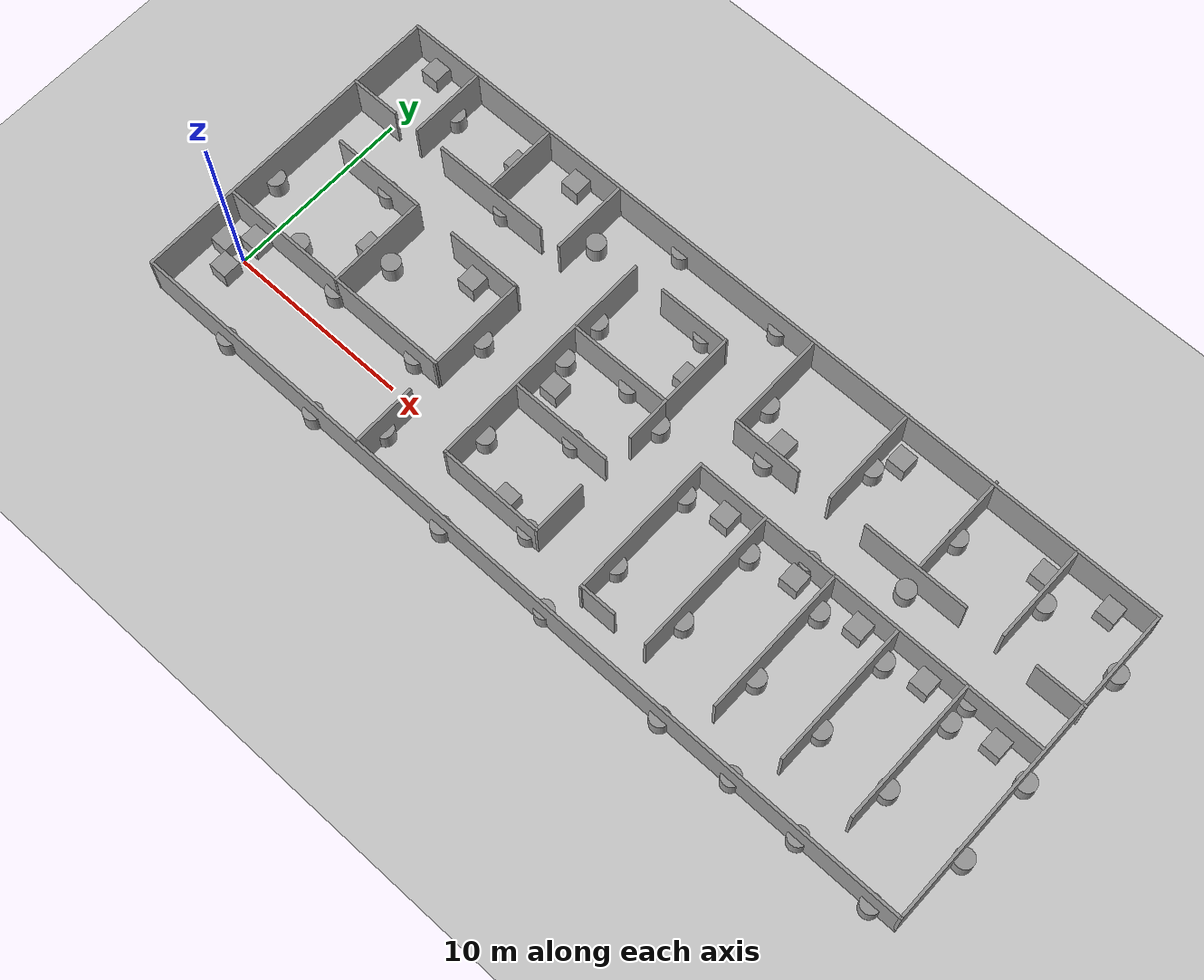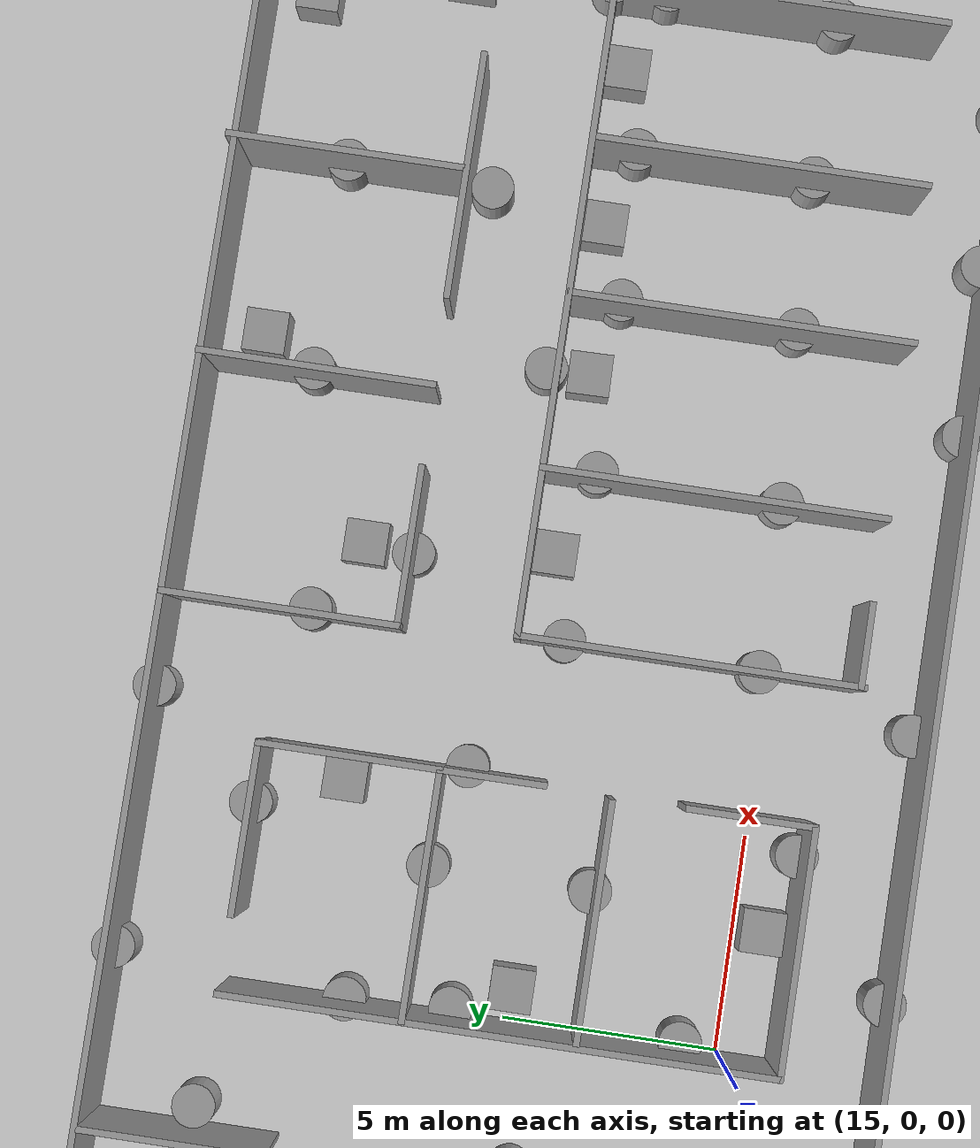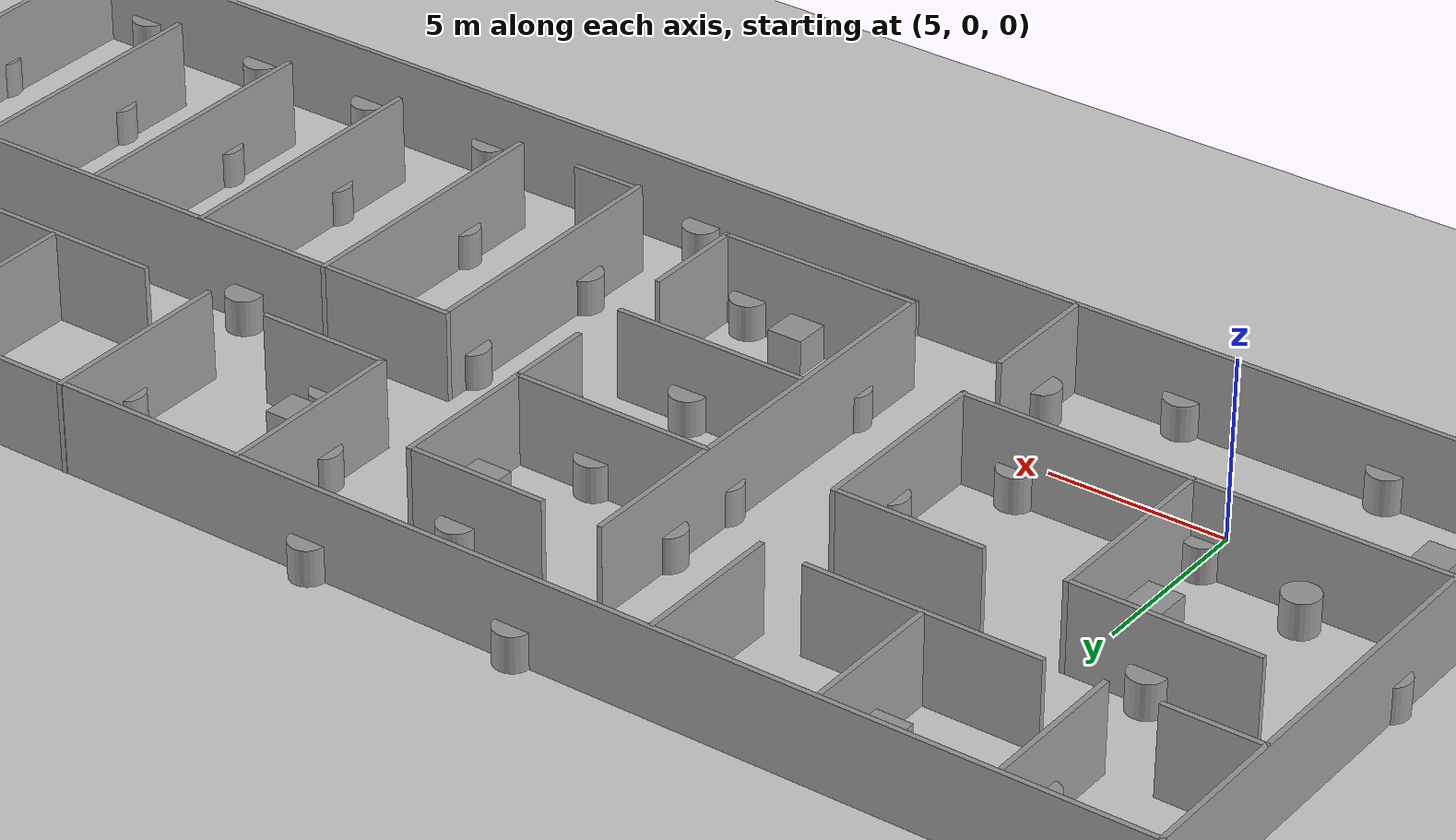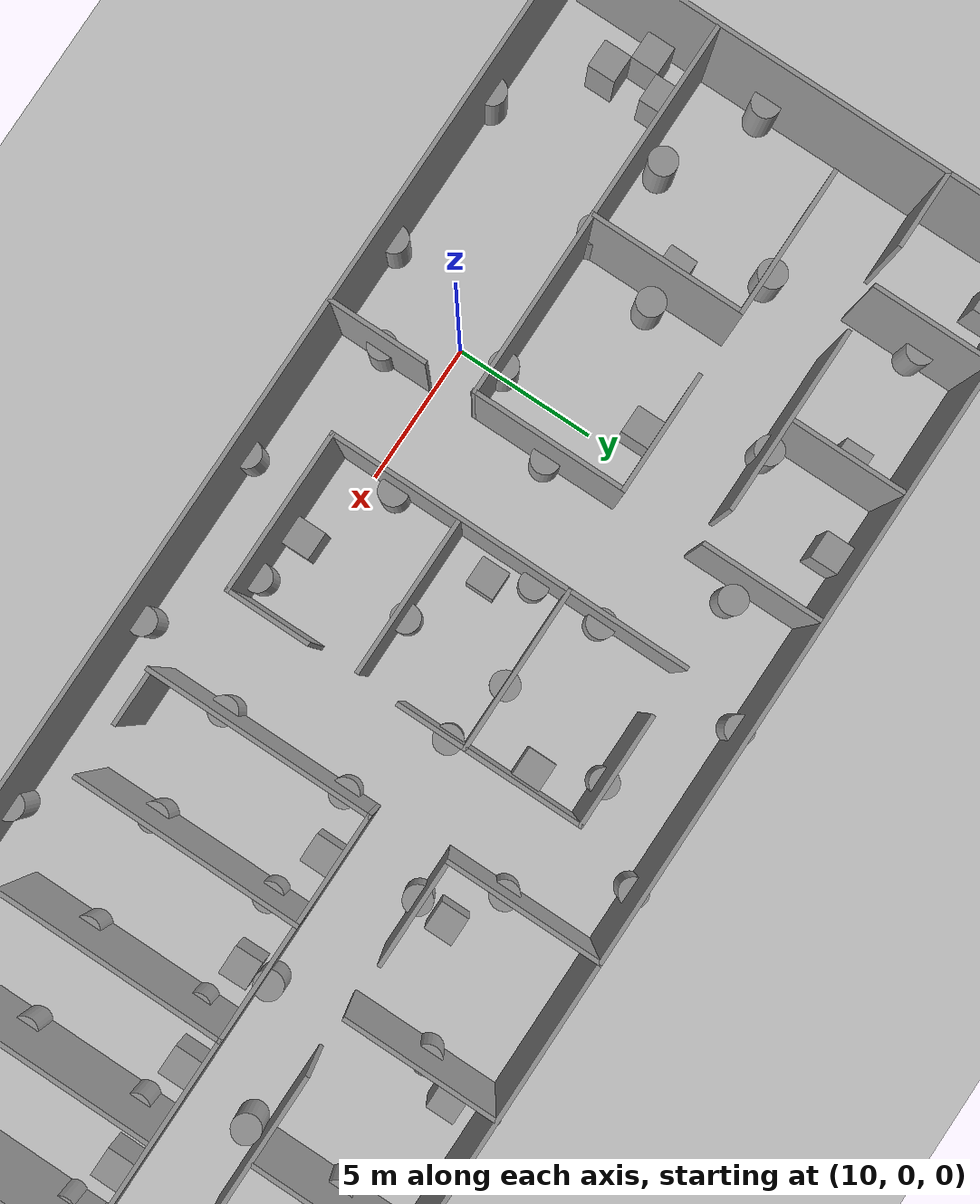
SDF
<sdf version="1.7">
 <world name="default">
  <light name="sun" type="directional">
   <pose>0 0 10 0 -0 0</pose>
   <diffuse>0.8 0.8 0.8 1</diffuse>
   <specular>0.2 0.2 0.2 1</specular>
   <attenuation>
    <range>1000</range>
    <constant>0.9</constant>
    <linear>0.01</linear>
    <quadratic>0.001</quadratic>
   </attenuation>
   <direction>-0.5 0.1 -0.9</direction>
   <spot><inner_angle>0</inner_angle><outer_angle>0</outer_angle><falloff>0</falloff></spot>
  </light>
  <model name="ground_plane">
   <static>1</static>
   <link name="link">
    <collision name="collision">
     <geometry><plane><normal>0 0 1</normal><size>100 100</size></plane></geometry>
     <surface>
      <contact><collide_bitmask>65535</collide_bitmask></contact>
      <friction><ode><mu>100</mu><mu2>50</mu2></ode></friction>
     </surface>
    </collision>
    <visual name="visual">
     <cast_shadows>0</cast_shadows>
     <geometry><plane><normal>0 0 1</normal><size>100 100</size></plane></geometry>
     <material>
      <script><uri>file://media/materials/scripts/gazebo.material</uri><name>Gazebo/Grey</name></script>
     </material>
    </visual>
   </link>
  </model>
  <gravity>0 0 -9.8</gravity>
  <magnetic_field>6e-06 2.3e-05 -4.2e-05</magnetic_field>
  <atmosphere type="adiabatic"/>
  <physics type="ode">
   <max_step_size>0.001</max_step_size>
   <real_time_factor>1</real_time_factor>
   <real_time_update_rate>1000</real_time_update_rate>
  </physics>
  <scene><ambient>0.4 0.4 0.4 1</ambient><background>0.7 0.7 0.7 1</background><shadows>1</shadows></scene>
  <spherical_coordinates>
   <surface_model>EARTH_WGS84</surface_model>
   <latitude_deg>0</latitude_deg>
   <longitude_deg>0</longitude_deg>
   <elevation>0</elevation>
   <heading_deg>0</heading_deg>
  </spherical_coordinates>
  <model name="Lab1">
   <pose>20.7319 5.29666 0 0 -0 0</pose>
   <link name="Wall_1">
    <collision name="Wall_1_Collision">
     <geometry><box><size>45.25 0.15 2.5</size></box></geometry>
     <pose>0 0 1.25 0 -0 0</pose>
    </collision>
    <visual name="Wall_1_Visual">
     <pose>0 0 1.25 0 -0 0</pose>
     <geometry><box><size>45.25 0.15 2.5</size></box></geometry>
     <material>
      <script><uri>file://media/materials/scripts/gazebo.material</uri><name>Gazebo/Grey</name></script>
      <ambient>1 1 1 1</ambient>
     </material>
     <meta><layer>0</layer></meta>
    </visual>
    <pose>-0.042167 -8.8672 0 0 -0 0</pose>
   </link>
   <link name="Wall_10">
    <collision name="Wall_10_Collision">
     <geometry><box><size>6.5 0.15 2.5</size></box></geometry>
     <pose>0 0 1.25 0 -0 0</pose>
    </collision>
    <visual name="Wall_10_Visual">
     <pose>0 0 1.25 0 -0 0</pose>
     <geometry><box><size>6.5 0.15 2.5</size></box></geometry>
     <material>
      <script><uri>file://media/materials/scripts/gazebo.material</uri><name>Gazebo/Grey</name></script>
      <ambient>1 1 1 1</ambient>
     </material>
     <meta><layer>0</layer></meta>
    </visual>
    <pose>-13.6987 4.60775 0 0 -0 0</pose>
   </link>
   <link name="Wall_12">
    <collision name="Wall_12_Collision">
     <geometry><box><size>4 0.15 2.5</size></box></geometry>
     <pose>0 0 1.25 0 -0 0</pose>
    </collision>
    <visual name="Wall_12_Visual">
     <pose>0 0 1.25 0 -0 0</pose>
     <geometry><box><size>4 0.15 2.5</size></box></geometry>
     <material>
      <script><uri>file://media/materials/scripts/gazebo.material</uri><name>Gazebo/Grey</name></script>
      <ambient>1 1 1 1</ambient>
     </material>
     <meta><layer>0</layer></meta>
    </visual>
    <pose>-13.7407 6.65442 0 0 -0 1.5708</pose>
   </link>
   <link name="Wall_14">
    <collision name="Wall_14_Collision">
     <geometry><box><size>4.25 0.15 2.5</size></box></geometry>
     <pose>0 0 1.25 0 -0 0</pose>
    </collision>
    <visual name="Wall_14_Visual">
     <pose>0 0 1.25 0 -0 0</pose>
     <geometry><box><size>4.25 0.15 2.5</size></box></geometry>
     <material>
      <script><uri>file://media/materials/scripts/gazebo.material</uri><name>Gazebo/Grey</name></script>
      <ambient>1 1 1 1</ambient>
     </material>
     <meta><layer>0</layer></meta>
    </visual>
    <pose>-9.17805 6.57286 0 0 -0 -1.5708</pose>
   </link>
   <link name="Wall_16">
    <collision name="Wall_16_Collision">
     <geometry><box><size>13.4461 0.15 2.5</size></box></geometry>
     <pose>0 0 1.25 0 -0 0</pose>
    </collision>
    <visual name="Wall_16_Visual">
     <pose>0 0 1.25 0 -0 0</pose>
     <geometry><box><size>13.4461 0.15 2.5</size></box></geometry>
     <material>
      <script><uri>file://media/materials/scripts/gazebo.material</uri><name>Gazebo/Grey</name></script>
      <ambient>1 1 1 1</ambient>
     </material>
     <meta><layer>0</layer></meta>
    </visual>
    <pose>-15.853 -3.71144 0 0 -0 0.002288</pose>
   </link>
   <link name="Wall_17">
    <collision name="Wall_17_Collision">
     <geometry><box><size>5.5 0.15 2.5</size></box></geometry>
     <pose>0 0 1.25 0 -0 0</pose>
    </collision>
    <visual name="Wall_17_Visual">
     <pose>0 0 1.25 0 -0 0</pose>
     <geometry><box><size>5.5 0.15 2.5</size></box></geometry>
     <material>
      <script><uri>file://media/materials/scripts/gazebo.material</uri><name>Gazebo/Grey</name></script>
      <ambient>1 1 1 1</ambient>
     </material>
     <meta><layer>0</layer></meta>
    </visual>
    <pose>-9.20509 -1.05165 0 0 -0 1.5708</pose>
   </link>
   <link name="Wall_19">
    <collision name="Wall_19_Collision">
     <geometry><box><size>4.25 0.15 2.5</size></box></geometry>
     <pose>0 0 1.25 0 -0 0</pose>
    </collision>
    <visual name="Wall_19_Visual">
     <pose>0 0 1.25 0 -0 0</pose>
     <geometry><box><size>4.25 0.15 2.5</size></box></geometry>
     <material>
      <script><uri>file://media/materials/scripts/gazebo.material</uri><name>Gazebo/Grey</name></script>
      <ambient>1 1 1 1</ambient>
     </material>
     <meta><layer>0</layer></meta>
    </visual>
    <pose>-11.2551 1.62335 0 0 -0 3.14159</pose>
   </link>
   <link name="Wall_2">
    <collision name="Wall_2_Collision">
     <geometry><box><size>17.75 0.15 2.5</size></box></geometry>
     <pose>0 0 1.25 0 -0 0</pose>
    </collision>
    <visual name="Wall_2_Visual">
     <pose>0 0 1.25 0 -0 0</pose>
     <geometry><box><size>17.75 0.15 2.5</size></box></geometry>
     <material>
      <script><uri>file://media/materials/scripts/gazebo.material</uri><name>Gazebo/Grey</name></script>
      <ambient>1 1 1 1</ambient>
     </material>
     <meta><layer>0</layer></meta>
    </visual>
    <pose>22.5078 -0.067203 0 0 -0 1.5708</pose>
   </link>
   <link name="Wall_21">
    <collision name="Wall_21_Collision">
     <geometry><box><size>5.5 0.15 2.5</size></box></geometry>
     <pose>0 0 1.25 0 -0 0</pose>
    </collision>
    <visual name="Wall_21_Visual">
     <pose>0 0 1.25 0 -0 0</pose>
     <geometry><box><size>5.5 0.15 2.5</size></box></geometry>
     <material>
      <script><uri>file://media/materials/scripts/gazebo.material</uri><name>Gazebo/Grey</name></script>
      <ambient>1 1 1 1</ambient>
     </material>
     <meta><layer>0</layer></meta>
    </visual>
    <pose>-15.6266 -1.04817 0 0 -0 -1.5708</pose>
   </link>
   <link name="Wall_23">
    <collision name="Wall_23_Collision">
     <geometry><box><size>5.25 0.15 2.5</size></box></geometry>
     <pose>0 0 1.25 0 -0 0</pose>
    </collision>
    <visual name="Wall_23_Visual">
     <pose>0 0 1.25 0 -0 0</pose>
     <geometry><box><size>5.25 0.15 2.5</size></box></geometry>
     <material>
      <script><uri>file://media/materials/scripts/gazebo.material</uri><name>Gazebo/Grey</name></script>
      <ambient>1 1 1 1</ambient>
     </material>
     <meta><layer>0</layer></meta>
    </visual>
    <pose>-18.1766 1.62683 0 0 -0 3.14159</pose>
   </link>
   <link name="Wall_25">
    <collision name="Wall_25_Collision">
     <geometry><box><size>3.5 0.15 2.5</size></box></geometry>
     <pose>0 0 1.25 0 -0 0</pose>
    </collision>
    <visual name="Wall_25_Visual">
     <pose>0 0 1.25 0 -0 0</pose>
     <geometry><box><size>3.5 0.15 2.5</size></box></geometry>
     <material>
      <script><uri>file://media/materials/scripts/gazebo.material</uri><name>Gazebo/Grey</name></script>
      <ambient>1 1 1 1</ambient>
     </material>
     <meta><layer>0</layer></meta>
    </visual>
    <pose>-9.11721 -7.13544 0 0 -0 -1.5708</pose>
   </link>
   <link name="Wall_27">
    <collision name="Wall_27_Collision">
     <geometry><box><size>12.75 0.15 2.5</size></box></geometry>
     <pose>0 0 1.25 0 -0 0</pose>
    </collision>
    <visual name="Wall_27_Visual">
     <pose>0 0 1.25 0 -0 0</pose>
     <geometry><box><size>12.75 0.15 2.5</size></box></geometry>
     <material>
      <script><uri>file://media/materials/scripts/gazebo.material</uri><name>Gazebo/Grey</name></script>
      <ambient>1 1 1 1</ambient>
     </material>
     <meta><layer>0</layer></meta>
    </visual>
    <pose>-5.80171 -0.232211 0 0 -0 -1.5708</pose>
   </link>
   <link name="Wall_28">
    <collision name="Wall_28_Collision">
     <geometry><box><size>5.75 0.15 2.5</size></box></geometry>
     <pose>0 0 1.25 0 -0 0</pose>
    </collision>
    <visual name="Wall_28_Visual">
     <pose>0 0 1.25 0 -0 0</pose>
     <geometry><box><size>5.75 0.15 2.5</size></box></geometry>
     <material>
      <script><uri>file://media/materials/scripts/gazebo.material</uri><name>Gazebo/Grey</name></script>
      <ambient>1 1 1 1</ambient>
     </material>
     <meta><layer>0</layer></meta>
    </visual>
    <pose>-3.00171 -6.53221 0 0 -0 0</pose>
   </link>
   <link name="Wall_29">
    <collision name="Wall_29_Collision">
     <geometry><box><size>3 0.15 2.5</size></box></geometry>
     <pose>0 0 1.25 0 -0 0</pose>
    </collision>
    <visual name="Wall_29_Visual">
     <pose>0 0 1.25 0 -0 0</pose>
     <geometry><box><size>3 0.15 2.5</size></box></geometry>
     <material>
      <script><uri>file://media/materials/scripts/gazebo.material</uri><name>Gazebo/Grey</name></script>
      <ambient>1 1 1 1</ambient>
     </material>
     <meta><layer>0</layer></meta>
    </visual>
    <pose>-0.201707 -5.10721 0 0 -0 1.5708</pose>
   </link>
   <link name="Wall_3">
    <collision name="Wall_3_Collision">
     <geometry><box><size>45.25 0.15 2.5</size></box></geometry>
     <pose>0 0 1.25 0 -0 0</pose>
    </collision>
    <visual name="Wall_3_Visual">
     <pose>0 0 1.25 0 -0 0</pose>
     <geometry><box><size>45.25 0.15 2.5</size></box></geometry>
     <material>
      <script><uri>file://media/materials/scripts/gazebo.material</uri><name>Gazebo/Grey</name></script>
      <ambient>1 1 1 1</ambient>
     </material>
     <meta><layer>0</layer></meta>
    </visual>
    <pose>-0.042167 8.7328 0 0 -0 3.14159</pose>
   </link>
   <link name="Wall_31">
    <collision name="Wall_31_Collision">
     <geometry><box><size>5.5 0.15 2.5</size></box></geometry>
     <pose>0 0 1.25 0 -0 0</pose>
    </collision>
    <visual name="Wall_31_Visual">
     <pose>0 0 1.25 0 -0 0</pose>
     <geometry><box><size>5.5 0.15 2.5</size></box></geometry>
     <material>
      <script><uri>file://media/materials/scripts/gazebo.material</uri><name>Gazebo/Grey</name></script>
      <ambient>1 1 1 1</ambient>
     </material>
     <meta><layer>0</layer></meta>
    </visual>
    <pose>-3.00504 -1.96243 0 0 -0 0</pose>
   </link>
   <link name="Wall_33">
    <collision name="Wall_33_Collision">
     <geometry><box><size>2.5 0.15 2.5</size></box></geometry>
     <pose>0 0 1.25 0 -0 0</pose>
    </collision>
    <visual name="Wall_33_Visual">
     <pose>0 0 1.25 0 -0 0</pose>
     <geometry><box><size>2.5 0.15 2.5</size></box></geometry>
     <material>
      <script><uri>file://media/materials/scripts/gazebo.material</uri><name>Gazebo/Grey</name></script>
      <ambient>1 1 1 1</ambient>
     </material>
     <meta><layer>0</layer></meta>
    </visual>
    <pose>-0.17447 0.763862 0 0 -0 1.5708</pose>
   </link>
   <link name="Wall_34">
    <collision name="Wall_34_Collision">
     <geometry><box><size>5.75 0.15 2.5</size></box></geometry>
     <pose>0 0 1.25 0 -0 0</pose>
    </collision>
    <visual name="Wall_34_Visual">
     <pose>0 0 1.25 0 -0 0</pose>
     <geometry><box><size>5.75 0.15 2.5</size></box></geometry>
     <material>
      <script><uri>file://media/materials/scripts/gazebo.material</uri><name>Gazebo/Grey</name></script>
      <ambient>1 1 1 1</ambient>
     </material>
     <meta><layer>0</layer></meta>
    </visual>
    <pose>-2.97447 1.93886 0 0 -0 3.14159</pose>
   </link>
   <link name="Wall_36">
    <collision name="Wall_36_Collision">
     <geometry><box><size>4.25 0.15 2.5</size></box></geometry>
     <pose>0 0 1.25 0 -0 0</pose>
    </collision>
    <visual name="Wall_36_Visual">
     <pose>0 0 1.25 0 -0 0</pose>
     <geometry><box><size>4.25 0.15 2.5</size></box></geometry>
     <material>
      <script><uri>file://media/materials/scripts/gazebo.material</uri><name>Gazebo/Grey</name></script>
      <ambient>1 1 1 1</ambient>
     </material>
     <meta><layer>0</layer></meta>
    </visual>
    <pose>-0.17447 3.98886 0 0 -0 1.5708</pose>
   </link>
   <link name="Wall_37">
    <collision name="Wall_37_Collision">
     <geometry><box><size>4 0.15 2.5</size></box></geometry>
     <pose>0 0 1.25 0 -0 0</pose>
    </collision>
    <visual name="Wall_37_Visual">
     <pose>0 0 1.25 0 -0 0</pose>
     <geometry><box><size>4 0.15 2.5</size></box></geometry>
     <material>
      <script><uri>file://media/materials/scripts/gazebo.material</uri><name>Gazebo/Grey</name></script>
      <ambient>1 1 1 1</ambient>
     </material>
     <meta><layer>0</layer></meta>
    </visual>
    <pose>-2.09947 6.03886 0 0 -0 3.14159</pose>
   </link>
   <link name="Wall_39">
    <collision name="Wall_39_Collision">
     <geometry><box><size>5.5 0.15 2.5</size></box></geometry>
     <pose>0 0 1.25 0 -0 0</pose>
    </collision>
    <visual name="Wall_39_Visual">
     <pose>0 0 1.25 0 -0 0</pose>
     <geometry><box><size>5.5 0.15 2.5</size></box></geometry>
     <material>
      <script><uri>file://media/materials/scripts/gazebo.material</uri><name>Gazebo/Grey</name></script>
      <ambient>1 1 1 1</ambient>
     </material>
     <meta><layer>0</layer></meta>
    </visual>
    <pose>2.86164 6.04835 0 0 -0 -1.5708</pose>
   </link>
   <link name="Wall_4">
    <collision name="Wall_4_Collision">
     <geometry><box><size>17.75 0.15 2.5</size></box></geometry>
     <pose>0 0 1.25 0 -0 0</pose>
    </collision>
    <visual name="Wall_4_Visual">
     <pose>0 0 1.25 0 -0 0</pose>
     <geometry><box><size>17.75 0.15 2.5</size></box></geometry>
     <material>
      <script><uri>file://media/materials/scripts/gazebo.material</uri><name>Gazebo/Grey</name></script>
      <ambient>1 1 1 1</ambient>
     </material>
     <meta><layer>0</layer></meta>
    </visual>
    <pose>-22.5922 -0.067203 0 0 -0 -1.5708</pose>
   </link>
   <link name="Wall_40">
    <collision name="Wall_40_Collision">
     <geometry><box><size>3.75 0.15 2.5</size></box></geometry>
     <pose>0 0 1.25 0 -0 0</pose>
    </collision>
    <visual name="Wall_40_Visual">
     <pose>0 0 1.25 0 -0 0</pose>
     <geometry><box><size>3.75 0.15 2.5</size></box></geometry>
     <material>
      <script><uri>file://media/materials/scripts/gazebo.material</uri><name>Gazebo/Grey</name></script>
      <ambient>1 1 1 1</ambient>
     </material>
     <meta><layer>0</layer></meta>
    </visual>
    <pose>4.66164 3.37335 0 0 -0 0</pose>
   </link>
   <link name="Wall_42">
    <collision name="Wall_42_Collision">
     <geometry><box><size>5.5 0.15 2.5</size></box></geometry>
     <pose>0 0 1.25 0 -0 0</pose>
    </collision>
    <visual name="Wall_42_Visual">
     <pose>0 0 1.25 0 -0 0</pose>
     <geometry><box><size>5.5 0.15 2.5</size></box></geometry>
     <material>
      <script><uri>file://media/materials/scripts/gazebo.material</uri><name>Gazebo/Grey</name></script>
      <ambient>1 1 1 1</ambient>
     </material>
     <meta><layer>0</layer></meta>
    </visual>
    <pose>8.35901 6.07831 0 0 -0 1.5708</pose>
   </link>
   <link name="Wall_44">
    <collision name="Wall_44_Collision">
     <geometry><box><size>5.75 0.15 2.5</size></box></geometry>
     <pose>0 0 1.25 0 -0 0</pose>
    </collision>
    <visual name="Wall_44_Visual">
     <pose>0 0 1.25 0 -0 0</pose>
     <geometry><box><size>5.75 0.15 2.5</size></box></geometry>
     <material>
      <script><uri>file://media/materials/scripts/gazebo.material</uri><name>Gazebo/Grey</name></script>
      <ambient>1 1 1 1</ambient>
     </material>
     <meta><layer>0</layer></meta>
    </visual>
    <pose>13.2161 3.40331 0 0 -0 0</pose>
   </link>
   <link name="Wall_46">
    <collision name="Wall_46_Collision">
     <geometry><box><size>5.25 0.15 2.5</size></box></geometry>
     <pose>0 0 1.25 0 -0 0</pose>
    </collision>
    <visual name="Wall_46_Visual">
     <pose>0 0 1.25 0 -0 0</pose>
     <geometry><box><size>5.25 0.15 2.5</size></box></geometry>
     <material>
      <script><uri>file://media/materials/scripts/gazebo.material</uri><name>Gazebo/Grey</name></script>
      <ambient>1 1 1 1</ambient>
     </material>
     <meta><layer>0</layer></meta>
    </visual>
    <pose>18.0415 6.09518 0 0 -0 1.5708</pose>
   </link>
   <link name="Wall_48">
    <collision name="Wall_48_Collision">
     <geometry><box><size>2.75 0.15 2.5</size></box></geometry>
     <pose>0 0 1.25 0 -0 0</pose>
    </collision>
    <visual name="Wall_48_Visual">
     <pose>0 0 1.25 0 -0 0</pose>
     <geometry><box><size>2.75 0.15 2.5</size></box></geometry>
     <material>
      <script><uri>file://media/materials/scripts/gazebo.material</uri><name>Gazebo/Grey</name></script>
      <ambient>1 1 1 1</ambient>
     </material>
     <meta><layer>0</layer></meta>
    </visual>
    <pose>21.2922 3.36784 0 0 -0 0</pose>
   </link>
   <link name="Wall_50">
    <collision name="Wall_50_Collision">
     <geometry><box><size>5.5 0.15 2.5</size></box></geometry>
     <pose>0 0 1.25 0 -0 0</pose>
    </collision>
    <visual name="Wall_50_Visual">
     <pose>0 0 1.25 0 -0 0</pose>
     <geometry><box><size>5.5 0.15 2.5</size></box></geometry>
     <material>
      <script><uri>file://media/materials/scripts/gazebo.material</uri><name>Gazebo/Grey</name></script>
      <ambient>1 1 1 1</ambient>
     </material>
     <meta><layer>0</layer></meta>
    </visual>
    <pose>13.3599 6.1922 0 0 -0 1.5708</pose>
   </link>
   <link name="Wall_52">
    <collision name="Wall_52_Collision">
     <geometry><box><size>19.5 0.15 2.5</size></box></geometry>
     <pose>0 0 1.25 0 -0 0</pose>
    </collision>
    <visual name="Wall_52_Visual">
     <pose>0 0 1.25 0 -0 0</pose>
     <geometry><box><size>19.5 0.15 2.5</size></box></geometry>
     <material>
      <script><uri>file://media/materials/scripts/gazebo.material</uri><name>Gazebo/Grey</name></script>
      <ambient>1 1 1 1</ambient>
     </material>
     <meta><layer>0</layer></meta>
    </visual>
    <pose>12.7236 0.684137 0 0 -0 0</pose>
   </link>
   <link name="Wall_54">
    <collision name="Wall_54_Collision">
     <geometry><box><size>7.75 0.15 2.5</size></box></geometry>
     <pose>0 0 1.25 0 -0 0</pose>
    </collision>
    <visual name="Wall_54_Visual">
     <pose>0 0 1.25 0 -0 0</pose>
     <geometry><box><size>7.75 0.15 2.5</size></box></geometry>
     <material>
      <script><uri>file://media/materials/scripts/gazebo.material</uri><name>Gazebo/Grey</name></script>
      <ambient>1 1 1 1</ambient>
     </material>
     <meta><layer>0</layer></meta>
    </visual>
    <pose>18.3182 -3.15064 0 0 -0 -1.5708</pose>
   </link>
   <link name="Wall_56">
    <collision name="Wall_56_Collision">
     <geometry><box><size>7.75 0.15 2.5</size></box></geometry>
     <pose>0 0 1.25 0 -0 0</pose>
    </collision>
    <visual name="Wall_56_Visual">
     <pose>0 0 1.25 0 -0 0</pose>
     <geometry><box><size>7.75 0.15 2.5</size></box></geometry>
     <material>
      <script><uri>file://media/materials/scripts/gazebo.material</uri><name>Gazebo/Grey</name></script>
      <ambient>1 1 1 1</ambient>
     </material>
     <meta><layer>0</layer></meta>
    </visual>
    <pose>14.5269 -3.22021 0 0 -0 -1.5708</pose>
   </link>
   <link name="Wall_58">
    <collision name="Wall_58_Collision">
     <geometry><box><size>8 0.15 2.5</size></box></geometry>
     <pose>0 0 1.25 0 -0 0</pose>
    </collision>
    <visual name="Wall_58_Visual">
     <pose>0 0 1.25 0 -0 0</pose>
     <geometry><box><size>8 0.15 2.5</size></box></geometry>
     <material>
      <script><uri>file://media/materials/scripts/gazebo.material</uri><name>Gazebo/Grey</name></script>
      <ambient>1 1 1 1</ambient>
     </material>
     <meta><layer>0</layer></meta>
    </visual>
    <pose>10.9095 -3.27564 0 0 -0 -1.5708</pose>
   </link>
   <link name="Wall_6">
    <collision name="Wall_6_Collision">
     <geometry><box><size>2.75 0.15 2.5</size></box></geometry>
     <pose>0 0 1.25 0 -0 0</pose>
    </collision>
    <visual name="Wall_6_Visual">
     <pose>0 0 1.25 0 -0 0</pose>
     <geometry><box><size>2.75 0.15 2.5</size></box></geometry>
     <material>
      <script><uri>file://media/materials/scripts/gazebo.material</uri><name>Gazebo/Grey</name></script>
      <ambient>1 1 1 1</ambient>
     </material>
     <meta><layer>0</layer></meta>
    </visual>
    <pose>-21.2617 4.48608 0 0 -0 0</pose>
   </link>
   <link name="Wall_60">
    <collision name="Wall_60_Collision">
     <geometry><box><size>8 0.15 2.5</size></box></geometry>
     <pose>0 0 1.25 0 -0 0</pose>
    </collision>
    <visual name="Wall_60_Visual">
     <pose>0 0 1.25 0 -0 0</pose>
     <geometry><box><size>8 0.15 2.5</size></box></geometry>
     <material>
      <script><uri>file://media/materials/scripts/gazebo.material</uri><name>Gazebo/Grey</name></script>
      <ambient>1 1 1 1</ambient>
     </material>
     <meta><layer>0</layer></meta>
    </visual>
    <pose>6.87471 -3.24086 0 0 -0 -1.5708</pose>
   </link>
   <link name="Wall_62">
    <collision name="Wall_62_Collision">
     <geometry><box><size>8 0.15 2.5</size></box></geometry>
     <pose>0 0 1.25 0 -0 0</pose>
    </collision>
    <visual name="Wall_62_Visual">
     <pose>0 0 1.25 0 -0 0</pose>
     <geometry><box><size>8 0.15 2.5</size></box></geometry>
     <material>
      <script><uri>file://media/materials/scripts/gazebo.material</uri><name>Gazebo/Grey</name></script>
      <ambient>1 1 1 1</ambient>
     </material>
     <meta><layer>0</layer></meta>
    </visual>
    <pose>3.04863 -3.24086 0 0 -0 -1.5708</pose>
   </link>
   <link name="Wall_64">
    <collision name="Wall_64_Collision">
     <geometry><box><size>2 0.15 2.5</size></box></geometry>
     <pose>0 0 1.25 0 -0 0</pose>
    </collision>
    <visual name="Wall_64_Visual">
     <pose>0 0 1.25 0 -0 0</pose>
     <geometry><box><size>2 0.15 2.5</size></box></geometry>
     <material>
      <script><uri>file://media/materials/scripts/gazebo.material</uri><name>Gazebo/Grey</name></script>
      <ambient>1 1 1 1</ambient>
     </material>
     <meta><layer>0</layer></meta>
    </visual>
    <pose>3.98819 -7.09369 0 0 -0 3.14159</pose>
   </link>
   <link name="Wall_8">
    <collision name="Wall_8_Collision">
     <geometry><box><size>4.25 0.15 2.5</size></box></geometry>
     <pose>0 0 1.25 0 -0 0</pose>
    </collision>
    <visual name="Wall_8_Visual">
     <pose>0 0 1.25 0 -0 0</pose>
     <geometry><box><size>4.25 0.15 2.5</size></box></geometry>
     <material>
      <script><uri>file://media/materials/scripts/gazebo.material</uri><name>Gazebo/Grey</name></script>
      <ambient>1 1 1 1</ambient>
     </material>
     <meta><layer>0</layer></meta>
    </visual>
    <pose>-18.4858 6.59691 0 0 -0 1.5708</pose>
   </link>
   <static>1</static>
  </model>
  <model name="unit_box">
   <pose>-0.024443 0.998995 0.499995 -0 1e-05 0.002284</pose>
   <link name="link">
    <inertial>
     <mass>1</mass>
     <inertia>
      <ixx>0.166667</ixx>
      <ixy>0</ixy>
      <ixz>0</ixz>
      <iyy>0.166667</iyy>
      <iyz>0</iyz>
      <izz>0.166667</izz>
     </inertia>
    </inertial>
    <collision name="collision"><geometry><box><size>1 1 1</size></box></geometry></collision>
    <visual name="visual">
     <geometry><box><size>1 1 1</size></box></geometry>
     <material>
      <script><name>Gazebo/Grey</name><uri>file://media/materials/scripts/gazebo.material</uri></script>
     </material>
    </visual>
   </link>
  </model>
  <model name="unit_box_0">
   <pose>-1.04246 0.03451 0.499995 0 1e-05 0</pose>
   <link name="link">
    <inertial>
     <mass>1</mass>
     <inertia>
      <ixx>0.166667</ixx>
      <ixy>0</ixy>
      <ixz>0</ixz>
      <iyy>0.166667</iyy>
      <iyz>0</iyz>
      <izz>0.166667</izz>
     </inertia>
    </inertial>
    <collision name="collision"><geometry><box><size>1 1 1</size></box></geometry></collision>
    <visual name="visual">
     <geometry><box><size>1 1 1</size></box></geometry>
     <material>
      <script><name>Gazebo/Grey</name><uri>file://media/materials/scripts/gazebo.material</uri></script>
     </material>
    </visual>
   </link>
  </model>
  <model name="unit_box_1">
   <pose>-0.055882 -0.96791 0.499995 1e-05 -0 0</pose>
   <link name="link">
    <inertial>
     <mass>1</mass>
     <inertia>
      <ixx>0.166667</ixx>
      <ixy>0</ixy>
      <ixz>0</ixz>
      <iyy>0.166667</iyy>
      <iyz>0</iyz>
      <izz>0.166667</izz>
     </inertia>
    </inertial>
    <collision name="collision"><geometry><box><size>1 1 1</size></box></geometry></collision>
    <visual name="visual">
     <geometry><box><size>1 1 1</size></box></geometry>
     <material>
      <script><name>Gazebo/Grey</name><uri>file://media/materials/scripts/gazebo.material</uri></script>
     </material>
    </visual>
   </link>
  </model>
  <model name="unit_cylinder">
   <pose>4.75919 1.58041 0.5 0 -0 0</pose>
   <link name="link">
    <inertial>
     <mass>1</mass>
     <inertia><ixx>0.145833</ixx><ixy>0</ixy><ixz>0</ixz><iyy>0.145833</iyy><iyz>0</iyz><izz>0.125</izz></inertia>
    </inertial>
    <collision name="collision">
     <geometry><cylinder><radius>0.5</radius><length>1</length></cylinder></geometry>
    </collision>
    <visual name="visual">
     <geometry><cylinder><radius>0.5</radius><length>1</length></cylinder></geometry>
     <material>
      <script><name>Gazebo/Grey</name><uri>file://media/materials/scripts/gazebo.material</uri></script>
     </material>
    </visual>
   </link>
  </model>
  <model name="unit_cylinder_0">
   <pose>2.80886 -3.54775 0.499996 3e-06 1e-06 -0</pose>
   <link name="link">
    <inertial>
     <mass>1</mass>
     <inertia><ixx>0.145833</ixx><ixy>0</ixy><ixz>0</ixz><iyy>0.145833</iyy><iyz>0</iyz><izz>0.125</izz></inertia>
    </inertial>
    <collision name="collision">
     <geometry><cylinder><radius>0.5</radius><length>1</length></cylinder></geometry>
    </collision>
    <visual name="visual">
     <geometry><cylinder><radius>0.5</radius><length>1</length></cylinder></geometry>
     <material>
      <script><name>Gazebo/Grey</name><uri>file://media/materials/scripts/gazebo.material</uri></script>
     </material>
    </visual>
   </link>
  </model>
  <model name="unit_cylinder_1">
   <pose>8.48238 -3.51303 0.499994 -3e-06 -1e-06 -0</pose>
   <link name="link">
    <inertial>
     <mass>1</mass>
     <inertia><ixx>0.145833</ixx><ixy>0</ixy><ixz>0</ixz><iyy>0.145833</iyy><iyz>0</iyz><izz>0.125</izz></inertia>
    </inertial>
    <collision name="collision">
     <geometry><cylinder><radius>0.5</radius><length>1</length></cylinder></geometry>
    </collision>
    <visual name="visual">
     <geometry><cylinder><radius>0.5</radius><length>1</length></cylinder></geometry>
     <material>
      <script><name>Gazebo/Grey</name><uri>file://media/materials/scripts/gazebo.material</uri></script>
     </material>
    </visual>
   </link>
  </model>
  <model name="unit_cylinder_2">
   <pose>9.93981 1.6283 0.499996 3e-06 1e-06 -0</pose>
   <link name="link">
    <inertial>
     <mass>1</mass>
     <inertia><ixx>0.145833</ixx><ixy>0</ixy><ixz>0</ixz><iyy>0.145833</iyy><iyz>0</iyz><izz>0.125</izz></inertia>
    </inertial>
    <collision name="collision">
     <geometry><cylinder><radius>0.5</radius><length>1</length></cylinder></geometry>
    </collision>
    <visual name="visual">
     <geometry><cylinder><radius>0.5</radius><length>1</length></cylinder></geometry>
     <material>
      <script><name>Gazebo/Grey</name><uri>file://media/materials/scripts/gazebo.material</uri></script>
     </material>
    </visual>
   </link>
  </model>
  <model name="unit_cylinder_3">
   <pose>16.7123 -3.57275 0.499997 -5e-06 -1e-06 0</pose>
   <link name="link">
    <inertial>
     <mass>1</mass>
     <inertia><ixx>0.145833</ixx><ixy>0</ixy><ixz>0</ixz><iyy>0.145833</iyy><iyz>0</iyz><izz>0.125</izz></inertia>
    </inertial>
    <collision name="collision">
     <geometry><cylinder><radius>0.5</radius><length>1</length></cylinder></geometry>
    </collision>
    <visual name="visual">
     <geometry><cylinder><radius>0.5</radius><length>1</length></cylinder></geometry>
     <material>
      <script><name>Gazebo/Grey</name><uri>file://media/materials/scripts/gazebo.material</uri></script>
     </material>
    </visual>
   </link>
  </model>
  <model name="unit_cylinder_4">
   <pose>19.7629 -1.10703 0.499991 -1e-06 -1e-06 0</pose>
   <link name="link">
    <inertial>
     <mass>1</mass>
     <inertia><ixx>0.145833</ixx><ixy>0</ixy><ixz>0</ixz><iyy>0.145833</iyy><iyz>0</iyz><izz>0.125</izz></inertia>
    </inertial>
    <collision name="collision">
     <geometry><cylinder><radius>0.5</radius><length>1</length></cylinder></geometry>
    </collision>
    <visual name="visual">
     <geometry><cylinder><radius>0.5</radius><length>1</length></cylinder></geometry>
     <material>
      <script><name>Gazebo/Grey</name><uri>file://media/materials/scripts/gazebo.material</uri></script>
     </material>
    </visual>
   </link>
  </model>
  <model name="unit_cylinder_5">
   <pose>22.8884 -3.35687 0.499997 -5e-06 -1e-06 0</pose>
   <link name="link">
    <inertial>
     <mass>1</mass>
     <inertia><ixx>0.145833</ixx><ixy>0</ixy><ixz>0</ixz><iyy>0.145833</iyy><iyz>0</iyz><izz>0.125</izz></inertia>
    </inertial>
    <collision name="collision">
     <geometry><cylinder><radius>0.5</radius><length>1</length></cylinder></geometry>
    </collision>
    <visual name="visual">
     <geometry><cylinder><radius>0.5</radius><length>1</length></cylinder></geometry>
     <material>
      <script><name>Gazebo/Grey</name><uri>file://media/materials/scripts/gazebo.material</uri></script>
     </material>
    </visual>
   </link>
  </model>
  <model name="unit_cylinder_6">
   <pose>11.6809 4.356 0.499991 -1e-06 -1e-06 0</pose>
   <link name="link">
    <inertial>
     <mass>1</mass>
     <inertia><ixx>0.145833</ixx><ixy>0</ixy><ixz>0</ixz><iyy>0.145833</iyy><iyz>0</iyz><izz>0.125</izz></inertia>
    </inertial>
    <collision name="collision">
     <geometry><cylinder><radius>0.5</radius><length>1</length></cylinder></geometry>
    </collision>
    <visual name="visual">
     <geometry><cylinder><radius>0.5</radius><length>1</length></cylinder></geometry>
     <material>
      <script><name>Gazebo/Grey</name><uri>file://media/materials/scripts/gazebo.material</uri></script>
     </material>
    </visual>
   </link>
  </model>
  <model name="unit_cylinder_7">
   <pose>15.1715 6.22916 0.499997 -5e-06 -1e-06 0</pose>
   <link name="link">
    <inertial>
     <mass>1</mass>
     <inertia><ixx>0.145833</ixx><ixy>0</ixy><ixz>0</ixz><iyy>0.145833</iyy><iyz>0</iyz><izz>0.125</izz></inertia>
    </inertial>
    <collision name="collision">
     <geometry><cylinder><radius>0.5</radius><length>1</length></cylinder></geometry>
    </collision>
    <visual name="visual">
     <geometry><cylinder><radius>0.5</radius><length>1</length></cylinder></geometry>
     <material>
      <script><name>Gazebo/Grey</name><uri>file://media/materials/scripts/gazebo.material</uri></script>
     </material>
    </visual>
   </link>
  </model>
  <model name="unit_cylinder_8">
   <pose>15.1671 0.927672 0.499991 -1e-06 -1e-06 0</pose>
   <link name="link">
    <inertial>
     <mass>1</mass>
     <inertia><ixx>0.145833</ixx><ixy>0</ixy><ixz>0</ixz><iyy>0.145833</iyy><iyz>0</iyz><izz>0.125</izz></inertia>
    </inertial>
    <collision name="collision">
     <geometry><cylinder><radius>0.5</radius><length>1</length></cylinder></geometry>
    </collision>
    <visual name="visual">
     <geometry><cylinder><radius>0.5</radius><length>1</length></cylinder></geometry>
     <material>
      <script><name>Gazebo/Grey</name><uri>file://media/materials/scripts/gazebo.material</uri></script>
     </material>
    </visual>
   </link>
  </model>
  <model name="unit_cylinder_9">
   <pose>18.3073 7.22307 0.499997 -5e-06 -1e-06 0</pose>
   <link name="link">
    <inertial>
     <mass>1</mass>
     <inertia><ixx>0.145833</ixx><ixy>0</ixy><ixz>0</ixz><iyy>0.145833</iyy><iyz>0</iyz><izz>0.125</izz></inertia>
    </inertial>
    <collision name="collision">
     <geometry><cylinder><radius>0.5</radius><length>1</length></cylinder></geometry>
    </collision>
    <visual name="visual">
     <geometry><cylinder><radius>0.5</radius><length>1</length></cylinder></geometry>
     <material>
      <script><name>Gazebo/Grey</name><uri>file://media/materials/scripts/gazebo.material</uri></script>
     </material>
    </visual>
   </link>
  </model>
  <model name="unit_cylinder_10">
   <pose>18.2706 3.46356 0.499996 3e-06 1e-06 -0</pose>
   <link name="link">
    <inertial>
     <mass>1</mass>
     <inertia><ixx>0.145833</ixx><ixy>0</ixy><ixz>0</ixz><iyy>0.145833</iyy><iyz>0</iyz><izz>0.125</izz></inertia>
    </inertial>
    <collision name="collision">
     <geometry><cylinder><radius>0.5</radius><length>1</length></cylinder></geometry>
    </collision>
    <visual name="visual">
     <geometry><cylinder><radius>0.5</radius><length>1</length></cylinder></geometry>
     <material>
      <script><name>Gazebo/Grey</name><uri>file://media/materials/scripts/gazebo.material</uri></script>
     </material>
    </visual>
   </link>
  </model>
  <model name="unit_cylinder_11">
   <pose>7.56625 10.0611 0.499998 3e-06 -1e-06 -1e-06</pose>
   <link name="link">
    <inertial>
     <mass>1</mass>
     <inertia><ixx>0.145833</ixx><ixy>0</ixy><ixz>0</ixz><iyy>0.145833</iyy><iyz>0</iyz><izz>0.125</izz></inertia>
    </inertial>
    <collision name="collision">
     <geometry><cylinder><radius>0.5</radius><length>1</length></cylinder></geometry>
    </collision>
    <visual name="visual">
     <geometry><cylinder><radius>0.5</radius><length>1</length></cylinder></geometry>
     <material>
      <script><name>Gazebo/Grey</name><uri>file://media/materials/scripts/gazebo.material</uri></script>
     </material>
    </visual>
   </link>
  </model>
  <model name="unit_cylinder_12">
   <pose>2.80703 7.07168 0.499996 3e-06 1e-06 -0</pose>
   <link name="link">
    <inertial>
     <mass>1</mass>
     <inertia><ixx>0.145833</ixx><ixy>0</ixy><ixz>0</ixz><iyy>0.145833</iyy><iyz>0</iyz><izz>0.125</izz></inertia>
    </inertial>
    <collision name="collision">
     <geometry><cylinder><radius>0.5</radius><length>1</length></cylinder></geometry>
    </collision>
    <visual name="visual">
     <geometry><cylinder><radius>0.5</radius><length>1</length></cylinder></geometry>
     <material>
      <script><name>Gazebo/Grey</name><uri>file://media/materials/scripts/gazebo.material</uri></script>
     </material>
    </visual>
   </link>
  </model>
  <model name="unit_cylinder_13">
   <pose>2.24485 12.2965 0.499994 -3e-06 -1e-06 -0</pose>
   <link name="link">
    <inertial>
     <mass>1</mass>
     <inertia><ixx>0.145833</ixx><ixy>0</ixy><ixz>0</ixz><iyy>0.145833</iyy><iyz>0</iyz><izz>0.125</izz></inertia>
    </inertial>
    <collision name="collision">
     <geometry><cylinder><radius>0.5</radius><length>1</length></cylinder></geometry>
    </collision>
    <visual name="visual">
     <geometry><cylinder><radius>0.5</radius><length>1</length></cylinder></geometry>
     <material>
      <script><name>Gazebo/Grey</name><uri>file://media/materials/scripts/gazebo.material</uri></script>
     </material>
    </visual>
   </link>
  </model>
  <model name="unit_cylinder_14">
   <pose>-1.66528 3.91287 0.499996 3e-06 1e-06 -0</pose>
   <link name="link">
    <inertial>
     <mass>1</mass>
     <inertia><ixx>0.145833</ixx><ixy>0</ixy><ixz>0</ixz><iyy>0.145833</iyy><iyz>0</iyz><izz>0.125</izz></inertia>
    </inertial>
    <collision name="collision">
     <geometry><cylinder><radius>0.5</radius><length>1</length></cylinder></geometry>
    </collision>
    <visual name="visual">
     <geometry><cylinder><radius>0.5</radius><length>1</length></cylinder></geometry>
     <material>
      <script><name>Gazebo/Grey</name><uri>file://media/materials/scripts/gazebo.material</uri></script>
     </material>
    </visual>
   </link>
  </model>
  <model name="unit_cylinder_15">
   <pose>19.1337 11.4714 0.5 0 -0 0</pose>
   <link name="link">
    <inertial>
     <mass>1</mass>
     <inertia><ixx>0.145833</ixx><ixy>0</ixy><ixz>0</ixz><iyy>0.145833</iyy><iyz>0</iyz><izz>0.125</izz></inertia>
    </inertial>
    <collision name="collision">
     <geometry><cylinder><radius>0.5</radius><length>1</length></cylinder></geometry>
    </collision>
    <visual name="visual">
     <geometry><cylinder><radius>0.5</radius><length>1</length></cylinder></geometry>
     <material>
      <script><name>Gazebo/Grey</name><uri>file://media/materials/scripts/gazebo.material</uri></script>
     </material>
    </visual>
   </link>
  </model>
  <model name="unit_cylinder_16">
   <pose>15.4224 14.0725 0.499996 3e-06 1e-06 -0</pose>
   <link name="link">
    <inertial>
     <mass>1</mass>
     <inertia><ixx>0.145833</ixx><ixy>0</ixy><ixz>0</ixz><iyy>0.145833</iyy><iyz>0</iyz><izz>0.125</izz></inertia>
    </inertial>
    <collision name="collision">
     <geometry><cylinder><radius>0.5</radius><length>1</length></cylinder></geometry>
    </collision>
    <visual name="visual">
     <geometry><cylinder><radius>0.5</radius><length>1</length></cylinder></geometry>
     <material>
      <script><name>Gazebo/Grey</name><uri>file://media/materials/scripts/gazebo.material</uri></script>
     </material>
    </visual>
   </link>
  </model>
  <model name="unit_cylinder_17">
   <pose>23.7386 10.803 0.499994 -3e-06 -1e-06 -0</pose>
   <link name="link">
    <inertial>
     <mass>1</mass>
     <inertia><ixx>0.145833</ixx><ixy>0</ixy><ixz>0</ixz><iyy>0.145833</iyy><iyz>0</iyz><izz>0.125</izz></inertia>
    </inertial>
    <collision name="collision">
     <geometry><cylinder><radius>0.5</radius><length>1</length></cylinder></geometry>
    </collision>
    <visual name="visual">
     <geometry><cylinder><radius>0.5</radius><length>1</length></cylinder></geometry>
     <material>
      <script><name>Gazebo/Grey</name><uri>file://media/materials/scripts/gazebo.material</uri></script>
     </material>
    </visual>
   </link>
  </model>
  <model name="unit_cylinder_18">
   <pose>20.6876 6.66355 0.499996 -3e-06 3e-06 -2e-06</pose>
   <link name="link">
    <inertial>
     <mass>1</mass>
     <inertia><ixx>0.145833</ixx><ixy>0</ixy><ixz>0</ixz><iyy>0.145833</iyy><iyz>0</iyz><izz>0.125</izz></inertia>
    </inertial>
    <collision name="collision">
     <geometry><cylinder><radius>0.5</radius><length>1</length></cylinder></geometry>
    </collision>
    <visual name="visual">
     <geometry><cylinder><radius>0.5</radius><length>1</length></cylinder></geometry>
     <material>
      <script><name>Gazebo/Grey</name><uri>file://media/materials/scripts/gazebo.material</uri></script>
     </material>
    </visual>
   </link>
  </model>
  <model name="unit_cylinder_19">
   <pose>23.8281 0.332783 0.499994 -3e-06 -1e-06 -0</pose>
   <link name="link">
    <inertial>
     <mass>1</mass>
     <inertia><ixx>0.145833</ixx><ixy>0</ixy><ixz>0</ixz><iyy>0.145833</iyy><iyz>0</iyz><izz>0.125</izz></inertia>
    </inertial>
    <collision name="collision">
     <geometry><cylinder><radius>0.5</radius><length>1</length></cylinder></geometry>
    </collision>
    <visual name="visual">
     <geometry><cylinder><radius>0.5</radius><length>1</length></cylinder></geometry>
     <material>
      <script><name>Gazebo/Grey</name><uri>file://media/materials/scripts/gazebo.material</uri></script>
     </material>
    </visual>
   </link>
  </model>
  <model name="unit_cylinder_20">
   <pose>23.8675 4.89288 0.499997 3e-06 2e-06 0</pose>
   <link name="link">
    <inertial>
     <mass>1</mass>
     <inertia><ixx>0.145833</ixx><ixy>0</ixy><ixz>0</ixz><iyy>0.145833</iyy><iyz>0</iyz><izz>0.125</izz></inertia>
    </inertial>
    <collision name="collision">
     <geometry><cylinder><radius>0.5</radius><length>1</length></cylinder></geometry>
    </collision>
    <visual name="visual">
     <geometry><cylinder><radius>0.5</radius><length>1</length></cylinder></geometry>
     <material>
      <script><name>Gazebo/Grey</name><uri>file://media/materials/scripts/gazebo.material</uri></script>
     </material>
    </visual>
   </link>
  </model>
  <model name="unit_cylinder_21">
   <pose>29.2741 11.5981 0.499994 -3e-06 -2e-06 0</pose>
   <link name="link">
    <inertial>
     <mass>1</mass>
     <inertia><ixx>0.145833</ixx><ixy>0</ixy><ixz>0</ixz><iyy>0.145833</iyy><iyz>0</iyz><izz>0.125</izz></inertia>
    </inertial>
    <collision name="collision">
     <geometry><cylinder><radius>0.5</radius><length>1</length></cylinder></geometry>
    </collision>
    <visual name="visual">
     <geometry><cylinder><radius>0.5</radius><length>1</length></cylinder></geometry>
     <material>
      <script><name>Gazebo/Grey</name><uri>file://media/materials/scripts/gazebo.material</uri></script>
     </material>
    </visual>
   </link>
  </model>
  <model name="unit_cylinder_22">
   <pose>27.8376 4.7217 0.499997 3e-06 2e-06 0</pose>
   <link name="link">
    <inertial>
     <mass>1</mass>
     <inertia><ixx>0.145833</ixx><ixy>0</ixy><ixz>0</ixz><iyy>0.145833</iyy><iyz>0</iyz><izz>0.125</izz></inertia>
    </inertial>
    <collision name="collision">
     <geometry><cylinder><radius>0.5</radius><length>1</length></cylinder></geometry>
    </collision>
    <visual name="visual">
     <geometry><cylinder><radius>0.5</radius><length>1</length></cylinder></geometry>
     <material>
      <script><name>Gazebo/Grey</name><uri>file://media/materials/scripts/gazebo.material</uri></script>
     </material>
    </visual>
   </link>
  </model>
  <model name="unit_cylinder_23">
   <pose>27.7679 0.370614 0.499994 -3e-06 -2e-06 0</pose>
   <link name="link">
    <inertial>
     <mass>1</mass>
     <inertia><ixx>0.145833</ixx><ixy>0</ixy><ixz>0</ixz><iyy>0.145833</iyy><iyz>0</iyz><izz>0.125</izz></inertia>
    </inertial>
    <collision name="collision">
     <geometry><cylinder><radius>0.5</radius><length>1</length></cylinder></geometry>
    </collision>
    <visual name="visual">
     <geometry><cylinder><radius>0.5</radius><length>1</length></cylinder></geometry>
     <material>
      <script><name>Gazebo/Grey</name><uri>file://media/materials/scripts/gazebo.material</uri></script>
     </material>
    </visual>
   </link>
  </model>
  <model name="unit_cylinder_24">
   <pose>31.9263 4.75221 0.499997 -3e-06 -2e-06 0</pose>
   <link name="link">
    <inertial>
     <mass>1</mass>
     <inertia><ixx>0.145833</ixx><ixy>0</ixy><ixz>0</ixz><iyy>0.145833</iyy><iyz>0</iyz><izz>0.125</izz></inertia>
    </inertial>
    <collision name="collision">
     <geometry><cylinder><radius>0.5</radius><length>1</length></cylinder></geometry>
    </collision>
    <visual name="visual">
     <geometry><cylinder><radius>0.5</radius><length>1</length></cylinder></geometry>
     <material>
      <script><name>Gazebo/Grey</name><uri>file://media/materials/scripts/gazebo.material</uri></script>
     </material>
    </visual>
   </link>
  </model>
  <model name="unit_cylinder_25">
   <pose>31.8619 0.582942 0.499997 3e-06 2e-06 0</pose>
   <link name="link">
    <inertial>
     <mass>1</mass>
     <inertia><ixx>0.145833</ixx><ixy>0</ixy><ixz>0</ixz><iyy>0.145833</iyy><iyz>0</iyz><izz>0.125</izz></inertia>
    </inertial>
    <collision name="collision">
     <geometry><cylinder><radius>0.5</radius><length>1</length></cylinder></geometry>
    </collision>
    <visual name="visual">
     <geometry><cylinder><radius>0.5</radius><length>1</length></cylinder></geometry>
     <material>
      <script><name>Gazebo/Grey</name><uri>file://media/materials/scripts/gazebo.material</uri></script>
     </material>
    </visual>
   </link>
  </model>
  <model name="unit_cylinder_26">
   <pose>35.507 4.90735 0.499997 3e-06 2e-06 0</pose>
   <link name="link">
    <inertial>
     <mass>1</mass>
     <inertia><ixx>0.145833</ixx><ixy>0</ixy><ixz>0</ixz><iyy>0.145833</iyy><iyz>0</iyz><izz>0.125</izz></inertia>
    </inertial>
    <collision name="collision">
     <geometry><cylinder><radius>0.5</radius><length>1</length></cylinder></geometry>
    </collision>
    <visual name="visual">
     <geometry><cylinder><radius>0.5</radius><length>1</length></cylinder></geometry>
     <material>
      <script><name>Gazebo/Grey</name><uri>file://media/materials/scripts/gazebo.material</uri></script>
     </material>
    </visual>
   </link>
  </model>
  <model name="unit_cylinder_27">
   <pose>35.4721 0.714644 0.499994 -3e-06 -2e-06 0</pose>
   <link name="link">
    <inertial>
     <mass>1</mass>
     <inertia><ixx>0.145833</ixx><ixy>0</ixy><ixz>0</ixz><iyy>0.145833</iyy><iyz>0</iyz><izz>0.125</izz></inertia>
    </inertial>
    <collision name="collision">
     <geometry><cylinder><radius>0.5</radius><length>1</length></cylinder></geometry>
    </collision>
    <visual name="visual">
     <geometry><cylinder><radius>0.5</radius><length>1</length></cylinder></geometry>
     <material>
      <script><name>Gazebo/Grey</name><uri>file://media/materials/scripts/gazebo.material</uri></script>
     </material>
    </visual>
   </link>
  </model>
  <model name="unit_cylinder_28">
   <pose>39.3731 4.72285 0.499997 3e-06 2e-06 0</pose>
   <link name="link">
    <inertial>
     <mass>1</mass>
     <inertia><ixx>0.145833</ixx><ixy>0</ixy><ixz>0</ixz><iyy>0.145833</iyy><iyz>0</iyz><izz>0.125</izz></inertia>
    </inertial>
    <collision name="collision">
     <geometry><cylinder><radius>0.5</radius><length>1</length></cylinder></geometry>
    </collision>
    <visual name="visual">
     <geometry><cylinder><radius>0.5</radius><length>1</length></cylinder></geometry>
     <material>
      <script><name>Gazebo/Grey</name><uri>file://media/materials/scripts/gazebo.material</uri></script>
     </material>
    </visual>
   </link>
  </model>
  <model name="unit_cylinder_29">
   <pose>39.2782 0.646206 0.499994 -3e-06 -2e-06 0</pose>
   <link name="link">
    <inertial>
     <mass>1</mass>
     <inertia><ixx>0.145833</ixx><ixy>0</ixy><ixz>0</ixz><iyy>0.145833</iyy><iyz>0</iyz><izz>0.125</izz></inertia>
    </inertial>
    <collision name="collision">
     <geometry><cylinder><radius>0.5</radius><length>1</length></cylinder></geometry>
    </collision>
    <visual name="visual">
     <geometry><cylinder><radius>0.5</radius><length>1</length></cylinder></geometry>
     <material>
      <script><name>Gazebo/Grey</name><uri>file://media/materials/scripts/gazebo.material</uri></script>
     </material>
    </visual>
   </link>
  </model>
  <model name="unit_cylinder_30">
   <pose>29.9393 -3.56031 0.499997 3e-06 2e-06 0</pose>
   <link name="link">
    <inertial>
     <mass>1</mass>
     <inertia><ixx>0.145833</ixx><ixy>0</ixy><ixz>0</ixz><iyy>0.145833</iyy><iyz>0</iyz><izz>0.125</izz></inertia>
    </inertial>
    <collision name="collision">
     <geometry><cylinder><radius>0.5</radius><length>1</length></cylinder></geometry>
    </collision>
    <visual name="visual">
     <geometry><cylinder><radius>0.5</radius><length>1</length></cylinder></geometry>
     <material>
      <script><name>Gazebo/Grey</name><uri>file://media/materials/scripts/gazebo.material</uri></script>
     </material>
    </visual>
   </link>
  </model>
  <model name="unit_cylinder_31">
   <pose>33.9627 -3.45402 0.499994 -3e-06 -2e-06 0</pose>
   <link name="link">
    <inertial>
     <mass>1</mass>
     <inertia><ixx>0.145833</ixx><ixy>0</ixy><ixz>0</ixz><iyy>0.145833</iyy><iyz>0</iyz><izz>0.125</izz></inertia>
    </inertial>
    <collision name="collision">
     <geometry><cylinder><radius>0.5</radius><length>1</length></cylinder></geometry>
    </collision>
    <visual name="visual">
     <geometry><cylinder><radius>0.5</radius><length>1</length></cylinder></geometry>
     <material>
      <script><name>Gazebo/Grey</name><uri>file://media/materials/scripts/gazebo.material</uri></script>
     </material>
    </visual>
   </link>
  </model>
  <model name="unit_cylinder_32">
   <pose>37.7582 -3.49242 0.499997 4e-06 2e-06 -0</pose>
   <link name="link">
    <inertial>
     <mass>1</mass>
     <inertia><ixx>0.145833</ixx><ixy>0</ixy><ixz>0</ixz><iyy>0.145833</iyy><iyz>0</iyz><izz>0.125</izz></inertia>
    </inertial>
    <collision name="collision">
     <geometry><cylinder><radius>0.5</radius><length>1</length></cylinder></geometry>
    </collision>
    <visual name="visual">
     <geometry><cylinder><radius>0.5</radius><length>1</length></cylinder></geometry>
     <material>
      <script><name>Gazebo/Grey</name><uri>file://media/materials/scripts/gazebo.material</uri></script>
     </material>
    </visual>
   </link>
  </model>
  <model name="unit_cylinder_33">
   <pose>41.8535 -3.61097 0.499994 -4e-06 -3e-06 -0</pose>
   <link name="link">
    <inertial>
     <mass>1</mass>
     <inertia><ixx>0.145833</ixx><ixy>0</ixy><ixz>0</ixz><iyy>0.145833</iyy><iyz>0</iyz><izz>0.125</izz></inertia>
    </inertial>
    <collision name="collision">
     <geometry><cylinder><radius>0.5</radius><length>1</length></cylinder></geometry>
    </collision>
    <visual name="visual">
     <geometry><cylinder><radius>0.5</radius><length>1</length></cylinder></geometry>
     <material>
      <script><name>Gazebo/Grey</name><uri>file://media/materials/scripts/gazebo.material</uri></script>
     </material>
    </visual>
   </link>
  </model>
  <model name="unit_cylinder_34">
   <pose>43.4707 4.84227 0.5 0 -0 0</pose>
   <link name="link">
    <inertial>
     <mass>1</mass>
     <inertia><ixx>0.145833</ixx><ixy>0</ixy><ixz>0</ixz><iyy>0.145833</iyy><iyz>0</iyz><izz>0.125</izz></inertia>
    </inertial>
    <collision name="collision">
     <geometry><cylinder><radius>0.5</radius><length>1</length></cylinder></geometry>
    </collision>
    <visual name="visual">
     <geometry><cylinder><radius>0.5</radius><length>1</length></cylinder></geometry>
     <material>
      <script><name>Gazebo/Grey</name><uri>file://media/materials/scripts/gazebo.material</uri></script>
     </material>
    </visual>
   </link>
  </model>
  <model name="unit_cylinder_35">
   <pose>43.5544 0.506139 0.499994 -4e-06 -3e-06 -0</pose>
   <link name="link">
    <inertial>
     <mass>1</mass>
     <inertia><ixx>0.145833</ixx><ixy>0</ixy><ixz>0</ixz><iyy>0.145833</iyy><iyz>0</iyz><izz>0.125</izz></inertia>
    </inertial>
    <collision name="collision">
     <geometry><cylinder><radius>0.5</radius><length>1</length></cylinder></geometry>
    </collision>
    <visual name="visual">
     <geometry><cylinder><radius>0.5</radius><length>1</length></cylinder></geometry>
     <material>
      <script><name>Gazebo/Grey</name><uri>file://media/materials/scripts/gazebo.material</uri></script>
     </material>
    </visual>
   </link>
  </model>
  <model name="unit_cylinder_36">
   <pose>34.257 11.5672 0.499994 -4e-06 -3e-06 -0</pose>
   <link name="link">
    <inertial>
     <mass>1</mass>
     <inertia><ixx>0.145833</ixx><ixy>0</ixy><ixz>0</ixz><iyy>0.145833</iyy><iyz>0</iyz><izz>0.125</izz></inertia>
    </inertial>
    <collision name="collision">
     <geometry><cylinder><radius>0.5</radius><length>1</length></cylinder></geometry>
    </collision>
    <visual name="visual">
     <geometry><cylinder><radius>0.5</radius><length>1</length></cylinder></geometry>
     <material>
      <script><name>Gazebo/Grey</name><uri>file://media/materials/scripts/gazebo.material</uri></script>
     </material>
    </visual>
   </link>
  </model>
  <model name="unit_cylinder_37">
   <pose>39.0648 11.7422 0.499997 4e-06 3e-06 -0</pose>
   <link name="link">
    <inertial>
     <mass>1</mass>
     <inertia><ixx>0.145833</ixx><ixy>0</ixy><ixz>0</ixz><iyy>0.145833</iyy><iyz>0</iyz><izz>0.125</izz></inertia>
    </inertial>
    <collision name="collision">
     <geometry><cylinder><radius>0.5</radius><length>1</length></cylinder></geometry>
    </collision>
    <visual name="visual">
     <geometry><cylinder><radius>0.5</radius><length>1</length></cylinder></geometry>
     <material>
      <script><name>Gazebo/Grey</name><uri>file://media/materials/scripts/gazebo.material</uri></script>
     </material>
    </visual>
   </link>
  </model>
  <model name="unit_cylinder_38">
   <pose>43.4124 11.3153 0.499997 4e-06 3e-06 -0</pose>
   <link name="link">
    <inertial>
     <mass>1</mass>
     <inertia><ixx>0.145833</ixx><ixy>0</ixy><ixz>0</ixz><iyy>0.145833</iyy><iyz>0</iyz><izz>0.125</izz></inertia>
    </inertial>
    <collision name="collision">
     <geometry><cylinder><radius>0.5</radius><length>1</length></cylinder></geometry>
    </collision>
    <visual name="visual">
     <geometry><cylinder><radius>0.5</radius><length>1</length></cylinder></geometry>
     <material>
      <script><name>Gazebo/Grey</name><uri>file://media/materials/scripts/gazebo.material</uri></script>
     </material>
    </visual>
   </link>
  </model>
  <model name="unit_cylinder_39">
   <pose>39.3894 6.0355 0.499994 -4e-06 -4e-06 -0</pose>
   <link name="link">
    <inertial>
     <mass>1</mass>
     <inertia><ixx>0.145833</ixx><ixy>0</ixy><ixz>0</ixz><iyy>0.145833</iyy><iyz>0</iyz><izz>0.125</izz></inertia>
    </inertial>
    <collision name="collision">
     <geometry><cylinder><radius>0.5</radius><length>1</length></cylinder></geometry>
    </collision>
    <visual name="visual">
     <geometry><cylinder><radius>0.5</radius><length>1</length></cylinder></geometry>
     <material>
      <script><name>Gazebo/Grey</name><uri>file://media/materials/scripts/gazebo.material</uri></script>
     </material>
    </visual>
   </link>
  </model>
  <model name="unit_cylinder_40">
   <pose>34.1057 8.12497 0.499994 -1e-06 -6e-06 0.00063</pose>
   <link name="link">
    <inertial>
     <mass>1</mass>
     <inertia><ixx>0.145833</ixx><ixy>0</ixy><ixz>0</ixz><iyy>0.145833</iyy><iyz>0</iyz><izz>0.125</izz></inertia>
    </inertial>
    <collision name="collision">
     <geometry><cylinder><radius>0.5</radius><length>1</length></cylinder></geometry>
    </collision>
    <visual name="visual">
     <geometry><cylinder><radius>0.5</radius><length>1</length></cylinder></geometry>
     <material>
      <script><name>Gazebo/Grey</name><uri>file://media/materials/scripts/gazebo.material</uri></script>
     </material>
    </visual>
   </link>
  </model>
  <model name="unit_cylinder_41">
   <pose>30.0835 6.24818 0.499997 3e-06 2e-06 -0.003425</pose>
   <link name="link">
    <inertial>
     <mass>1</mass>
     <inertia><ixx>0.145833</ixx><ixy>0</ixy><ixz>0</ixz><iyy>0.145833</iyy><iyz>0</iyz><izz>0.125</izz></inertia>
    </inertial>
    <collision name="collision">
     <geometry><cylinder><radius>0.5</radius><length>1</length></cylinder></geometry>
    </collision>
    <visual name="visual">
     <geometry><cylinder><radius>0.5</radius><length>1</length></cylinder></geometry>
     <material>
      <script><name>Gazebo/Grey</name><uri>file://media/materials/scripts/gazebo.material</uri></script>
     </material>
    </visual>
   </link>
  </model>
  <model name="unit_cylinder_42">
   <pose>25.3497 8.64343 0.499994 -4e-06 -3e-06 0.056303</pose>
   <link name="link">
    <inertial>
     <mass>1</mass>
     <inertia><ixx>0.145833</ixx><ixy>0</ixy><ixz>0</ixz><iyy>0.145833</iyy><iyz>0</iyz><izz>0.125</izz></inertia>
    </inertial>
    <collision name="collision">
     <geometry><cylinder><radius>0.5</radius><length>1</length></cylinder></geometry>
    </collision>
    <visual name="visual">
     <geometry><cylinder><radius>0.5</radius><length>1</length></cylinder></geometry>
     <material>
      <script><name>Gazebo/Grey</name><uri>file://media/materials/scripts/gazebo.material</uri></script>
     </material>
    </visual>
   </link>
  </model>
  <model name="unit_cylinder_43">
   <pose>15.029 8.65559 0.499998 3e-06 4e-06 -0</pose>
   <link name="link">
    <inertial>
     <mass>1</mass>
     <inertia><ixx>0.145833</ixx><ixy>0</ixy><ixz>0</ixz><iyy>0.145833</iyy><iyz>0</iyz><izz>0.125</izz></inertia>
    </inertial>
    <collision name="collision">
     <geometry><cylinder><radius>0.5</radius><length>1</length></cylinder></geometry>
    </collision>
    <visual name="visual">
     <geometry><cylinder><radius>0.5</radius><length>1</length></cylinder></geometry>
     <material>
      <script><name>Gazebo/Grey</name><uri>file://media/materials/scripts/gazebo.material</uri></script>
     </material>
    </visual>
   </link>
  </model>
  <model name="unit_cylinder_44">
   <pose>12.1289 11.6841 0.499996 -2e-06 -3e-06 0</pose>
   <link name="link">
    <inertial>
     <mass>1</mass>
     <inertia><ixx>0.145833</ixx><ixy>0</ixy><ixz>0</ixz><iyy>0.145833</iyy><iyz>0</iyz><izz>0.125</izz></inertia>
    </inertial>
    <collision name="collision">
     <geometry><cylinder><radius>0.5</radius><length>1</length></cylinder></geometry>
    </collision>
    <visual name="visual">
     <geometry><cylinder><radius>0.5</radius><length>1</length></cylinder></geometry>
     <material>
      <script><name>Gazebo/Grey</name><uri>file://media/materials/scripts/gazebo.material</uri></script>
     </material>
    </visual>
   </link>
  </model>
  <model name="unit_cylinder_45">
   <pose>5.68034 4.37407 0.499995 3e-06 -1e-06 0.002304</pose>
   <link name="link">
    <inertial>
     <mass>1</mass>
     <inertia><ixx>0.145833</ixx><ixy>0</ixy><ixz>0</ixz><iyy>0.145833</iyy><iyz>0</iyz><izz>0.125</izz></inertia>
    </inertial>
    <collision name="collision">
     <geometry><cylinder><radius>0.5</radius><length>1</length></cylinder></geometry>
    </collision>
    <visual name="visual">
     <geometry><cylinder><radius>0.5</radius><length>1</length></cylinder></geometry>
     <material>
      <script><name>Gazebo/Grey</name><uri>file://media/materials/scripts/gazebo.material</uri></script>
     </material>
    </visual>
   </link>
  </model>
  <model name="unit_cylinder_46">
   <pose>1.7013 2.21769 0.499998 1e-06 -0 -8.1e-05</pose>
   <link name="link">
    <inertial>
     <mass>1</mass>
     <inertia><ixx>0.145833</ixx><ixy>0</ixy><ixz>0</ixz><iyy>0.145833</iyy><iyz>0</iyz><izz>0.125</izz></inertia>
    </inertial>
    <collision name="collision">
     <geometry><cylinder><radius>0.5</radius><length>1</length></cylinder></geometry>
    </collision>
    <visual name="visual">
     <geometry><cylinder><radius>0.5</radius><length>1</length></cylinder></geometry>
     <material>
      <script><name>Gazebo/Grey</name><uri>file://media/materials/scripts/gazebo.material</uri></script>
     </material>
    </visual>
   </link>
  </model>
  <model name="unit_box_2">
   <pose>-0.230579 13.4512 0.499995 -1e-05 0 0</pose>
   <link name="link">
    <inertial>
     <mass>1</mass>
     <inertia>
      <ixx>0.166667</ixx>
      <ixy>0</ixy>
      <ixz>0</ixz>
      <iyy>0.166667</iyy>
      <iyz>0</iyz>
      <izz>0.166667</izz>
     </inertia>
    </inertial>
    <collision name="collision"><geometry><box><size>1 1 1</size></box></geometry></collision>
    <visual name="visual">
     <geometry><box><size>1 1 1</size></box></geometry>
     <material>
      <script><name>Gazebo/Grey</name><uri>file://media/materials/scripts/gazebo.material</uri></script>
     </material>
    </visual>
   </link>
  </model>
  <model name="unit_box_3">
   <pose>4.29302 4.39081 0.5 0 0 -0.016202</pose>
   <link name="link">
    <inertial>
     <mass>1</mass>
     <inertia>
      <ixx>0.166667</ixx>
      <ixy>0</ixy>
      <ixz>0</ixz>
      <iyy>0.166667</iyy>
      <iyz>0</iyz>
      <izz>0.166667</izz>
     </inertia>
    </inertial>
    <collision name="collision"><geometry><box><size>1 1 1</size></box></geometry></collision>
    <visual name="visual">
     <geometry><box><size>1 1 1</size></box></geometry>
     <material>
      <script><name>Gazebo/Grey</name><uri>file://media/materials/scripts/gazebo.material</uri></script>
     </material>
    </visual>
   </link>
  </model>
  <model name="unit_box_4">
   <pose>6.38007 12.3734 0.499995 -0 -1e-05 -1e-06</pose>
   <link name="link">
    <inertial>
     <mass>1</mass>
     <inertia>
      <ixx>0.166667</ixx>
      <ixy>0</ixy>
      <ixz>0</ixz>
      <iyy>0.166667</iyy>
      <iyz>0</iyz>
      <izz>0.166667</izz>
     </inertia>
    </inertial>
    <collision name="collision"><geometry><box><size>1 1 1</size></box></geometry></collision>
    <visual name="visual">
     <geometry><box><size>1 1 1</size></box></geometry>
     <material>
      <script><name>Gazebo/Grey</name><uri>file://media/materials/scripts/gazebo.material</uri></script>
     </material>
    </visual>
   </link>
  </model>
  <model name="unit_box_5">
   <pose>9.14125 6.34501 0.499995 -1e-05 -0 0</pose>
   <link name="link">
    <inertial>
     <mass>1</mass>
     <inertia>
      <ixx>0.166667</ixx>
      <ixy>0</ixy>
      <ixz>0</ixz>
      <iyy>0.166667</iyy>
      <iyz>0</iyz>
      <izz>0.166667</izz>
     </inertia>
    </inertial>
    <collision name="collision"><geometry><box><size>1 1 1</size></box></geometry></collision>
    <visual name="visual">
     <geometry><box><size>1 1 1</size></box></geometry>
     <material>
      <script><name>Gazebo/Grey</name><uri>file://media/materials/scripts/gazebo.material</uri></script>
     </material>
    </visual>
   </link>
  </model>
  <model name="unit_box_6">
   <pose>9.16987 13.4545 0.5 0 -0 0</pose>
   <link name="link">
    <inertial>
     <mass>1</mass>
     <inertia>
      <ixx>0.166667</ixx>
      <ixy>0</ixy>
      <ixz>0</ixz>
      <iyy>0.166667</iyy>
      <iyz>0</iyz>
      <izz>0.166667</izz>
     </inertia>
    </inertial>
    <collision name="collision"><geometry><box><size>1 1 1</size></box></geometry></collision>
    <visual name="visual">
     <geometry><box><size>1 1 1</size></box></geometry>
     <material>
      <script><name>Gazebo/Grey</name><uri>file://media/materials/scripts/gazebo.material</uri></script>
     </material>
    </visual>
   </link>
  </model>
  <model name="unit_box_7">
   <pose>15.795 4.90815 0.499995 -1e-05 -0 -0</pose>
   <link name="link">
    <inertial>
     <mass>1</mass>
     <inertia>
      <ixx>0.166667</ixx>
      <ixy>0</ixy>
      <ixz>0</ixz>
      <iyy>0.166667</iyy>
      <iyz>0</iyz>
      <izz>0.166667</izz>
     </inertia>
    </inertial>
    <collision name="collision"><geometry><box><size>1 1 1</size></box></geometry></collision>
    <visual name="visual">
     <geometry><box><size>1 1 1</size></box></geometry>
     <material>
      <script><name>Gazebo/Grey</name><uri>file://media/materials/scripts/gazebo.material</uri></script>
     </material>
    </visual>
   </link>
  </model>
  <model name="unit_box_8">
   <pose>17.9409 -0.591387 0.499995 0 1e-05 0</pose>
   <link name="link">
    <inertial>
     <mass>1</mass>
     <inertia>
      <ixx>0.166667</ixx>
      <ixy>0</ixy>
      <ixz>0</ixz>
      <iyy>0.166667</iyy>
      <iyz>0</iyz>
      <izz>0.166667</izz>
     </inertia>
    </inertial>
    <collision name="collision"><geometry><box><size>1 1 1</size></box></geometry></collision>
    <visual name="visual">
     <geometry><box><size>1 1 1</size></box></geometry>
     <material>
      <script><name>Gazebo/Grey</name><uri>file://media/materials/scripts/gazebo.material</uri></script>
     </material>
    </visual>
   </link>
  </model>
  <model name="unit_box_9">
   <pose>19.9825 9.41852 0.499995 -0 1e-05 1e-06</pose>
   <link name="link">
    <inertial>
     <mass>1</mass>
     <inertia>
      <ixx>0.166667</ixx>
      <ixy>0</ixy>
      <ixz>0</ixz>
      <iyy>0.166667</iyy>
      <iyz>0</iyz>
      <izz>0.166667</izz>
     </inertia>
    </inertial>
    <collision name="collision"><geometry><box><size>1 1 1</size></box></geometry></collision>
    <visual name="visual">
     <geometry><box><size>1 1 1</size></box></geometry>
     <material>
      <script><name>Gazebo/Grey</name><uri>file://media/materials/scripts/gazebo.material</uri></script>
     </material>
    </visual>
   </link>
  </model>
  <model name="unit_box_10">
   <pose>25.8503 5.39619 0.499995 0 1e-05 0</pose>
   <link name="link">
    <inertial>
     <mass>1</mass>
     <inertia>
      <ixx>0.166667</ixx>
      <ixy>0</ixy>
      <ixz>0</ixz>
      <iyy>0.166667</iyy>
      <iyz>0</iyz>
      <izz>0.166667</izz>
     </inertia>
    </inertial>
    <collision name="collision"><geometry><box><size>1 1 1</size></box></geometry></collision>
    <visual name="visual">
     <geometry><box><size>1 1 1</size></box></geometry>
     <material>
      <script><name>Gazebo/Grey</name><uri>file://media/materials/scripts/gazebo.material</uri></script>
     </material>
    </visual>
   </link>
  </model>
  <model name="unit_box_11">
   <pose>30.106 5.22927 0.5 0 -0 0.016809</pose>
   <link name="link">
    <inertial>
     <mass>1</mass>
     <inertia>
      <ixx>0.166667</ixx>
      <ixy>0</ixy>
      <ixz>0</ixz>
      <iyy>0.166667</iyy>
      <iyz>0</iyz>
      <izz>0.166667</izz>
     </inertia>
    </inertial>
    <collision name="collision"><geometry><box><size>1 1 1</size></box></geometry></collision>
    <visual name="visual">
     <geometry><box><size>1 1 1</size></box></geometry>
     <material>
      <script><name>Gazebo/Grey</name><uri>file://media/materials/scripts/gazebo.material</uri></script>
     </material>
    </visual>
   </link>
  </model>
  <model name="unit_box_12">
   <pose>33.6726 5.38909 0.499995 0 1e-05 0</pose>
   <link name="link">
    <inertial>
     <mass>1</mass>
     <inertia>
      <ixx>0.166667</ixx>
      <ixy>0</ixy>
      <ixz>0</ixz>
      <iyy>0.166667</iyy>
      <iyz>0</iyz>
      <izz>0.166667</izz>
     </inertia>
    </inertial>
    <collision name="collision"><geometry><box><size>1 1 1</size></box></geometry></collision>
    <visual name="visual">
     <geometry><box><size>1 1 1</size></box></geometry>
     <material>
      <script><name>Gazebo/Grey</name><uri>file://media/materials/scripts/gazebo.material</uri></script>
     </material>
    </visual>
   </link>
  </model>
  <model name="unit_box_13">
   <pose>37.3999 5.40579 0.499995 1e-05 -0 0</pose>
   <link name="link">
    <inertial>
     <mass>1</mass>
     <inertia>
      <ixx>0.166667</ixx>
      <ixy>0</ixy>
      <ixz>0</ixz>
      <iyy>0.166667</iyy>
      <iyz>0</iyz>
      <izz>0.166667</izz>
     </inertia>
    </inertial>
    <collision name="collision"><geometry><box><size>1 1 1</size></box></geometry></collision>
    <visual name="visual">
     <geometry><box><size>1 1 1</size></box></geometry>
     <material>
      <script><name>Gazebo/Grey</name><uri>file://media/materials/scripts/gazebo.material</uri></script>
     </material>
    </visual>
   </link>
  </model>
  <model name="unit_box_14">
   <pose>41.4714 5.33217 0.499995 0 1e-05 0</pose>
   <link name="link">
    <inertial>
     <mass>1</mass>
     <inertia>
      <ixx>0.166667</ixx>
      <ixy>0</ixy>
      <ixz>0</ixz>
      <iyy>0.166667</iyy>
      <iyz>0</iyz>
      <izz>0.166667</izz>
     </inertia>
    </inertial>
    <collision name="collision"><geometry><box><size>1 1 1</size></box></geometry></collision>
    <visual name="visual">
     <geometry><box><size>1 1 1</size></box></geometry>
     <material>
      <script><name>Gazebo/Grey</name><uri>file://media/materials/scripts/gazebo.material</uri></script>
     </material>
    </visual>
   </link>
  </model>
  <model name="unit_box_15">
   <pose>41.4035 13.4544 0.5 -1e-06 -0 -7e-06</pose>
   <link name="link">
    <inertial>
     <mass>1</mass>
     <inertia>
      <ixx>0.166667</ixx>
      <ixy>0</ixy>
      <ixz>0</ixz>
      <iyy>0.166667</iyy>
      <iyz>0</iyz>
      <izz>0.166667</izz>
     </inertia>
    </inertial>
    <collision name="collision"><geometry><box><size>1 1 1</size></box></geometry></collision>
    <visual name="visual">
     <geometry><box><size>1 1 1</size></box></geometry>
     <material>
      <script><name>Gazebo/Grey</name><uri>file://media/materials/scripts/gazebo.material</uri></script>
     </material>
    </visual>
   </link>
  </model>
  <model name="unit_box_16">
   <pose>38.1984 12.8667 0.499995 0 1e-05 0</pose>
   <link name="link">
    <inertial>
     <mass>1</mass>
     <inertia>
      <ixx>0.166667</ixx>
      <ixy>0</ixy>
      <ixz>0</ixz>
      <iyy>0.166667</iyy>
      <iyz>0</iyz>
      <izz>0.166667</izz>
     </inertia>
    </inertial>
    <collision name="collision"><geometry><box><size>1 1 1</size></box></geometry></collision>
    <visual name="visual">
     <geometry><box><size>1 1 1</size></box></geometry>
     <material>
      <script><name>Gazebo/Grey</name><uri>file://media/materials/scripts/gazebo.material</uri></script>
     </material>
    </visual>
   </link>
  </model>
  <model name="unit_box_17">
   <pose>29.9782 12.8514 0.499995 -1e-05 -0 -0</pose>
   <link name="link">
    <inertial>
     <mass>1</mass>
     <inertia>
      <ixx>0.166667</ixx>
      <ixy>0</ixy>
      <ixz>0</ixz>
      <iyy>0.166667</iyy>
      <iyz>0</iyz>
      <izz>0.166667</izz>
     </inertia>
    </inertial>
    <collision name="collision"><geometry><box><size>1 1 1</size></box></geometry></collision>
    <visual name="visual">
     <geometry><box><size>1 1 1</size></box></geometry>
     <material>
      <script><name>Gazebo/Grey</name><uri>file://media/materials/scripts/gazebo.material</uri></script>
     </material>
    </visual>
   </link>
  </model>
  <model name="unit_box_18">
   <pose>25.4515 9.78208 0.499995 0 1e-05 0</pose>
   <link name="link">
    <inertial>
     <mass>1</mass>
     <inertia>
      <ixx>0.166667</ixx>
      <ixy>0</ixy>
      <ixz>0</ixz>
      <iyy>0.166667</iyy>
      <iyz>0</iyz>
      <izz>0.166667</izz>
     </inertia>
    </inertial>
    <collision name="collision"><geometry><box><size>1 1 1</size></box></geometry></collision>
    <visual name="visual">
     <geometry><box><size>1 1 1</size></box></geometry>
     <material>
      <script><name>Gazebo/Grey</name><uri>file://media/materials/scripts/gazebo.material</uri></script>
     </material>
    </visual>
   </link>
  </model>
  <model name="unit_cylinder_47">
   <pose>11.521 -1.93864 0.499993 -3e-06 -4e-06 -0</pose>
   <link name="link">
    <inertial>
     <mass>1</mass>
     <inertia><ixx>0.145833</ixx><ixy>0</ixy><ixz>0</ixz><iyy>0.145833</iyy><iyz>0</iyz><izz>0.125</izz></inertia>
    </inertial>
    <collision name="collision">
     <geometry><cylinder><radius>0.5</radius><length>1</length></cylinder></geometry>
    </collision>
    <visual name="visual">
     <geometry><cylinder><radius>0.5</radius><length>1</length></cylinder></geometry>
     <material>
      <script><name>Gazebo/Grey</name><uri>file://media/materials/scripts/gazebo.material</uri></script>
     </material>
    </visual>
   </link>
  </model>
  <model name="unit_cylinder_48">
   <pose>21.4603 14.0922 0.499997 3e-06 4e-06 -0</pose>
   <link name="link">
    <inertial>
     <mass>1</mass>
     <inertia><ixx>0.145833</ixx><ixy>0</ixy><ixz>0</ixz><iyy>0.145833</iyy><iyz>0</iyz><izz>0.125</izz></inertia>
    </inertial>
    <collision name="collision">
     <geometry><cylinder><radius>0.5</radius><length>1</length></cylinder></geometry>
    </collision>
    <visual name="visual">
     <geometry><cylinder><radius>0.5</radius><length>1</length></cylinder></geometry>
     <material>
      <script><name>Gazebo/Grey</name><uri>file://media/materials/scripts/gazebo.material</uri></script>
     </material>
    </visual>
   </link>
  </model>
 </world>
</sdf>
